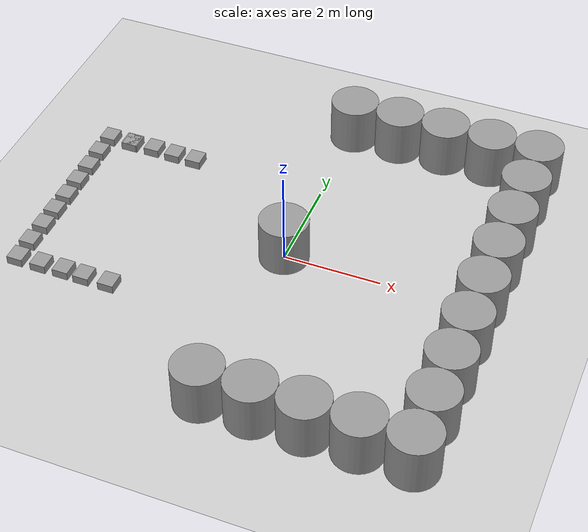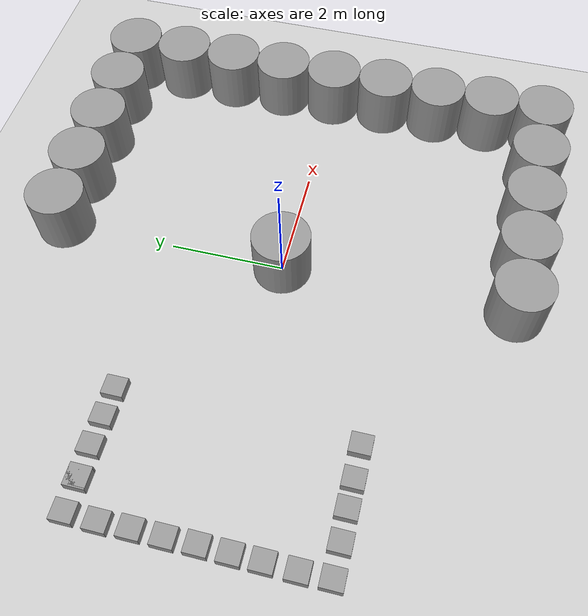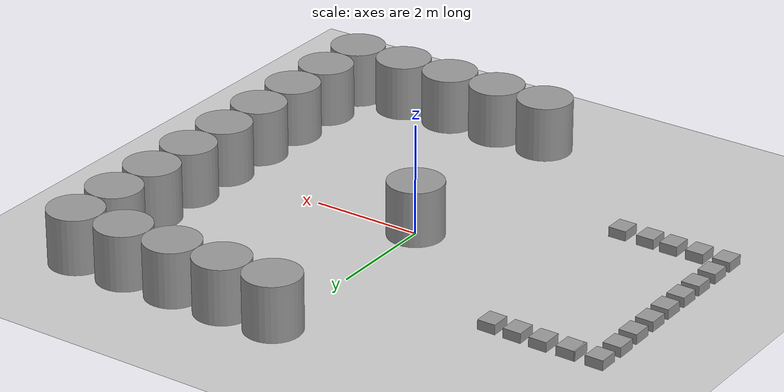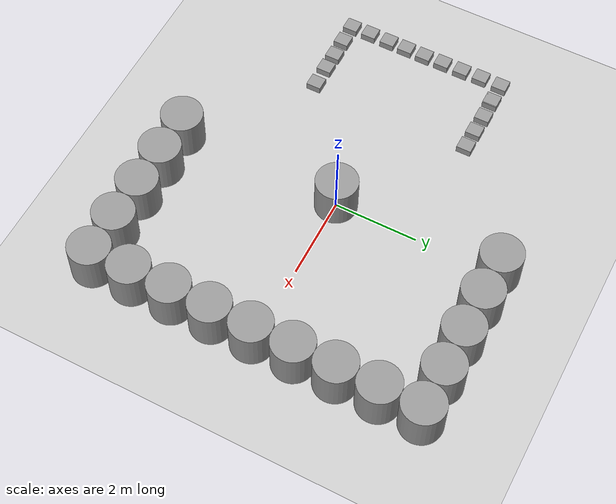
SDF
<sdf version="1.7">
 <world name="default">
  <light name="sun" type="directional">
   <pose>0 0 10 0 -0 0</pose>
   <diffuse>0.8 0.8 0.8 1</diffuse>
   <specular>0.2 0.2 0.2 1</specular>
   <attenuation>
    <range>1000</range>
    <constant>0.9</constant>
    <linear>0.01</linear>
    <quadratic>0.001</quadratic>
   </attenuation>
   <direction>-0.5 0.1 -0.9</direction>
   <spot><inner_angle>0</inner_angle><outer_angle>0</outer_angle><falloff>0</falloff></spot>
  </light>
  <model name="ground_plane">
   <static>1</static>
   <link name="link">
    <collision name="collision">
     <geometry><plane><normal>0 0 1</normal><size>100 100</size></plane></geometry>
     <surface>
      <contact><collide_bitmask>65535</collide_bitmask></contact>
      <friction><ode><mu>100</mu><mu2>50</mu2></ode></friction>
     </surface>
    </collision>
    <visual name="visual">
     <cast_shadows>0</cast_shadows>
     <geometry><plane><normal>0 0 1</normal><size>100 100</size></plane></geometry>
     <material>
      <script><uri>file://media/materials/scripts/gazebo.material</uri><name>Gazebo/Grey</name></script>
     </material>
    </visual>
   </link>
  </model>
  <gravity>0 0 -9.8</gravity>
  <magnetic_field>6e-06 2.3e-05 -4.2e-05</magnetic_field>
  <atmosphere type="adiabatic"/>
  <physics type="ode">
   <max_step_size>0.001</max_step_size>
   <real_time_factor>1</real_time_factor>
   <real_time_update_rate>1000</real_time_update_rate>
  </physics>
  <scene><ambient>0.4 0.4 0.4 1</ambient><background>0.7 0.7 0.7 1</background><shadows>1</shadows></scene>
  <spherical_coordinates>
   <surface_model>EARTH_WGS84</surface_model>
   <latitude_deg>0</latitude_deg>
   <longitude_deg>0</longitude_deg>
   <elevation>0</elevation>
   <heading_deg>0</heading_deg>
  </spherical_coordinates>
  <model name="cylinder_1m">
   <model name="cylinder_1m">
    <link name="link_0">
     <inertial>
      <mass>1</mass>
      <inertia>
       <ixx>0.166667</ixx>
       <ixy>0</ixy>
       <ixz>0</ixz>
       <iyy>0.166667</iyy>
       <iyz>0</iyz>
       <izz>0.166667</izz>
      </inertia>
     </inertial>
     <pose>0 0 -0 1.5708 -0 0</pose>
     <visual name="visual">
      <geometry>
       <mesh>
        <uri>/home/leesirius/workbench_ws/src/tb3_custom_worlds/custom_models/cylinder_1m.obj</uri>
        <scale>1 1 1</scale>
       </mesh>
      </geometry>
      <material>
       <lighting>1</lighting>
       <script><uri>file://media/materials/scripts/gazebo.material</uri><name>Gazebo/Grey</name></script>
       <shader type="pixel"/>
      </material>
     </visual>
     <collision name="collision">
      <geometry>
       <mesh>
        <uri>/home/leesirius/workbench_ws/src/tb3_custom_worlds/custom_models/cylinder_1m.obj</uri>
        <scale>1 1 1</scale>
       </mesh>
      </geometry>
      <surface>
       <friction>
        <ode><mu>1</mu><mu2>1</mu2><fdir1>0 0 0</fdir1><slip1>0</slip1><slip2>0</slip2></ode>
        <torsional>
         <coefficient>1</coefficient>
         <patch_radius>0</patch_radius>
         <surface_radius>0</surface_radius>
         <use_patch_radius>1</use_patch_radius>
         <ode><slip>0</slip></ode>
        </torsional>
       </friction>
       <bounce><restitution_coefficient>0</restitution_coefficient><threshold>1e+06</threshold></bounce>
       <contact>
        <collide_without_contact>0</collide_without_contact>
        <collide_without_contact_bitmask>1</collide_without_contact_bitmask>
        <collide_bitmask>1</collide_bitmask>
        <ode>
         <soft_cfm>0</soft_cfm>
         <soft_erp>0.2</soft_erp>
         <kp>1e+13</kp>
         <kd>1</kd>
         <max_vel>0.01</max_vel>
         <min_depth>0</min_depth>
        </ode>
        <bullet>
         <split_impulse>1</split_impulse>
         <split_impulse_penetration_threshold>-0.01</split_impulse_penetration_threshold>
         <soft_cfm>0</soft_cfm>
         <soft_erp>0.2</soft_erp>
         <kp>1e+13</kp>
         <kd>1</kd>
        </bullet>
       </contact>
      </surface>
     </collision>
    </link>
    <static>0</static>
    <pose>0 0 4e-06 0 -0 0</pose>
   </model>
   <static>1</static>
   <pose>0.000129 4.00143 0.499996 -3e-06 0 0.000269</pose>
  </model>
  <model name="cylinder_1m_clone">
   <model name="cylinder_1m">
    <link name="link_0">
     <inertial>
      <mass>1</mass>
      <inertia>
       <ixx>0.166667</ixx>
       <ixy>0</ixy>
       <ixz>0</ixz>
       <iyy>0.166667</iyy>
       <iyz>0</iyz>
       <izz>0.166667</izz>
      </inertia>
     </inertial>
     <pose>0 0 -0 1.5708 -0 0</pose>
     <visual name="visual">
      <geometry>
       <mesh>
        <uri>/home/leesirius/workbench_ws/src/tb3_custom_worlds/custom_models/cylinder_1m.obj</uri>
        <scale>1 1 1</scale>
       </mesh>
      </geometry>
      <material>
       <lighting>1</lighting>
       <script><uri>file://media/materials/scripts/gazebo.material</uri><name>Gazebo/Grey</name></script>
       <shader type="pixel"/>
      </material>
     </visual>
     <collision name="collision">
      <geometry>
       <mesh>
        <uri>/home/leesirius/workbench_ws/src/tb3_custom_worlds/custom_models/cylinder_1m.obj</uri>
        <scale>1 1 1</scale>
       </mesh>
      </geometry>
      <surface>
       <friction>
        <ode><mu>1</mu><mu2>1</mu2><fdir1>0 0 0</fdir1><slip1>0</slip1><slip2>0</slip2></ode>
        <torsional>
         <coefficient>1</coefficient>
         <patch_radius>0</patch_radius>
         <surface_radius>0</surface_radius>
         <use_patch_radius>1</use_patch_radius>
         <ode><slip>0</slip></ode>
        </torsional>
       </friction>
       <bounce><restitution_coefficient>0</restitution_coefficient><threshold>1e+06</threshold></bounce>
       <contact>
        <collide_without_contact>0</collide_without_contact>
        <collide_without_contact_bitmask>1</collide_without_contact_bitmask>
        <collide_bitmask>1</collide_bitmask>
        <ode>
         <soft_cfm>0</soft_cfm>
         <soft_erp>0.2</soft_erp>
         <kp>1e+13</kp>
         <kd>1</kd>
         <max_vel>0.01</max_vel>
         <min_depth>0</min_depth>
        </ode>
        <bullet>
         <split_impulse>1</split_impulse>
         <split_impulse_penetration_threshold>-0.01</split_impulse_penetration_threshold>
         <soft_cfm>0</soft_cfm>
         <soft_erp>0.2</soft_erp>
         <kp>1e+13</kp>
         <kd>1</kd>
        </bullet>
       </contact>
      </surface>
     </collision>
    </link>
    <static>0</static>
    <pose>0 0 4e-06 0 -0 0</pose>
   </model>
   <static>1</static>
   <pose>1.00003 3.99999 0.499993 -4e-06 -7e-06 0.000153</pose>
  </model>
  <model name="cylinder_1m_clone_0">
   <model name="cylinder_1m">
    <link name="link_0">
     <inertial>
      <mass>1</mass>
      <inertia>
       <ixx>0.166667</ixx>
       <ixy>0</ixy>
       <ixz>0</ixz>
       <iyy>0.166667</iyy>
       <iyz>0</iyz>
       <izz>0.166667</izz>
      </inertia>
     </inertial>
     <pose>0 0 -0 1.5708 -0 0</pose>
     <visual name="visual">
      <geometry>
       <mesh>
        <uri>/home/leesirius/workbench_ws/src/tb3_custom_worlds/custom_models/cylinder_1m.obj</uri>
        <scale>1 1 1</scale>
       </mesh>
      </geometry>
      <material>
       <lighting>1</lighting>
       <script><uri>file://media/materials/scripts/gazebo.material</uri><name>Gazebo/Grey</name></script>
       <shader type="pixel"/>
      </material>
     </visual>
     <collision name="collision">
      <geometry>
       <mesh>
        <uri>/home/leesirius/workbench_ws/src/tb3_custom_worlds/custom_models/cylinder_1m.obj</uri>
        <scale>1 1 1</scale>
       </mesh>
      </geometry>
      <surface>
       <friction>
        <ode><mu>1</mu><mu2>1</mu2><fdir1>0 0 0</fdir1><slip1>0</slip1><slip2>0</slip2></ode>
        <torsional>
         <coefficient>1</coefficient>
         <patch_radius>0</patch_radius>
         <surface_radius>0</surface_radius>
         <use_patch_radius>1</use_patch_radius>
         <ode><slip>0</slip></ode>
        </torsional>
       </friction>
       <bounce><restitution_coefficient>0</restitution_coefficient><threshold>1e+06</threshold></bounce>
       <contact>
        <collide_without_contact>0</collide_without_contact>
        <collide_without_contact_bitmask>1</collide_without_contact_bitmask>
        <collide_bitmask>1</collide_bitmask>
        <ode>
         <soft_cfm>0</soft_cfm>
         <soft_erp>0.2</soft_erp>
         <kp>1e+13</kp>
         <kd>1</kd>
         <max_vel>0.01</max_vel>
         <min_depth>0</min_depth>
        </ode>
        <bullet>
         <split_impulse>1</split_impulse>
         <split_impulse_penetration_threshold>-0.01</split_impulse_penetration_threshold>
         <soft_cfm>0</soft_cfm>
         <soft_erp>0.2</soft_erp>
         <kp>1e+13</kp>
         <kd>1</kd>
        </bullet>
       </contact>
      </surface>
     </collision>
    </link>
    <static>0</static>
    <pose>0 0 4e-06 0 -0 0</pose>
   </model>
   <static>1</static>
   <pose>2.00003 3.99999 0.499993 -4e-06 -7e-06 0.000153</pose>
  </model>
  <model name="cylinder_1m_clone_1">
   <model name="cylinder_1m">
    <link name="link_0">
     <inertial>
      <mass>1</mass>
      <inertia>
       <ixx>0.166667</ixx>
       <ixy>0</ixy>
       <ixz>0</ixz>
       <iyy>0.166667</iyy>
       <iyz>0</iyz>
       <izz>0.166667</izz>
      </inertia>
     </inertial>
     <pose>0 0 -0 1.5708 -0 0</pose>
     <visual name="visual">
      <geometry>
       <mesh>
        <uri>/home/leesirius/workbench_ws/src/tb3_custom_worlds/custom_models/cylinder_1m.obj</uri>
        <scale>1 1 1</scale>
       </mesh>
      </geometry>
      <material>
       <lighting>1</lighting>
       <script><uri>file://media/materials/scripts/gazebo.material</uri><name>Gazebo/Grey</name></script>
       <shader type="pixel"/>
      </material>
     </visual>
     <collision name="collision">
      <geometry>
       <mesh>
        <uri>/home/leesirius/workbench_ws/src/tb3_custom_worlds/custom_models/cylinder_1m.obj</uri>
        <scale>1 1 1</scale>
       </mesh>
      </geometry>
      <surface>
       <friction>
        <ode><mu>1</mu><mu2>1</mu2><fdir1>0 0 0</fdir1><slip1>0</slip1><slip2>0</slip2></ode>
        <torsional>
         <coefficient>1</coefficient>
         <patch_radius>0</patch_radius>
         <surface_radius>0</surface_radius>
         <use_patch_radius>1</use_patch_radius>
         <ode><slip>0</slip></ode>
        </torsional>
       </friction>
       <bounce><restitution_coefficient>0</restitution_coefficient><threshold>1e+06</threshold></bounce>
       <contact>
        <collide_without_contact>0</collide_without_contact>
        <collide_without_contact_bitmask>1</collide_without_contact_bitmask>
        <collide_bitmask>1</collide_bitmask>
        <ode>
         <soft_cfm>0</soft_cfm>
         <soft_erp>0.2</soft_erp>
         <kp>1e+13</kp>
         <kd>1</kd>
         <max_vel>0.01</max_vel>
         <min_depth>0</min_depth>
        </ode>
        <bullet>
         <split_impulse>1</split_impulse>
         <split_impulse_penetration_threshold>-0.01</split_impulse_penetration_threshold>
         <soft_cfm>0</soft_cfm>
         <soft_erp>0.2</soft_erp>
         <kp>1e+13</kp>
         <kd>1</kd>
        </bullet>
       </contact>
      </surface>
     </collision>
    </link>
    <static>0</static>
    <pose>0 0 4e-06 0 -0 0</pose>
   </model>
   <static>1</static>
   <pose>3.00003 3.99999 0.499993 -4e-06 -7e-06 0.000153</pose>
  </model>
  <model name="cylinder_1m_clone_2">
   <model name="cylinder_1m">
    <link name="link_0">
     <inertial>
      <mass>1</mass>
      <inertia>
       <ixx>0.166667</ixx>
       <ixy>0</ixy>
       <ixz>0</ixz>
       <iyy>0.166667</iyy>
       <iyz>0</iyz>
       <izz>0.166667</izz>
      </inertia>
     </inertial>
     <pose>0 0 -0 1.5708 -0 0</pose>
     <visual name="visual">
      <geometry>
       <mesh>
        <uri>/home/leesirius/workbench_ws/src/tb3_custom_worlds/custom_models/cylinder_1m.obj</uri>
        <scale>1 1 1</scale>
       </mesh>
      </geometry>
      <material>
       <lighting>1</lighting>
       <script><uri>file://media/materials/scripts/gazebo.material</uri><name>Gazebo/Grey</name></script>
       <shader type="pixel"/>
      </material>
     </visual>
     <collision name="collision">
      <geometry>
       <mesh>
        <uri>/home/leesirius/workbench_ws/src/tb3_custom_worlds/custom_models/cylinder_1m.obj</uri>
        <scale>1 1 1</scale>
       </mesh>
      </geometry>
      <surface>
       <friction>
        <ode><mu>1</mu><mu2>1</mu2><fdir1>0 0 0</fdir1><slip1>0</slip1><slip2>0</slip2></ode>
        <torsional>
         <coefficient>1</coefficient>
         <patch_radius>0</patch_radius>
         <surface_radius>0</surface_radius>
         <use_patch_radius>1</use_patch_radius>
         <ode><slip>0</slip></ode>
        </torsional>
       </friction>
       <bounce><restitution_coefficient>0</restitution_coefficient><threshold>1e+06</threshold></bounce>
       <contact>
        <collide_without_contact>0</collide_without_contact>
        <collide_without_contact_bitmask>1</collide_without_contact_bitmask>
        <collide_bitmask>1</collide_bitmask>
        <ode>
         <soft_cfm>0</soft_cfm>
         <soft_erp>0.2</soft_erp>
         <kp>1e+13</kp>
         <kd>1</kd>
         <max_vel>0.01</max_vel>
         <min_depth>0</min_depth>
        </ode>
        <bullet>
         <split_impulse>1</split_impulse>
         <split_impulse_penetration_threshold>-0.01</split_impulse_penetration_threshold>
         <soft_cfm>0</soft_cfm>
         <soft_erp>0.2</soft_erp>
         <kp>1e+13</kp>
         <kd>1</kd>
        </bullet>
       </contact>
      </surface>
     </collision>
    </link>
    <static>0</static>
    <pose>0 0 4e-06 0 -0 0</pose>
   </model>
   <static>1</static>
   <pose>4.00003 3.99999 0.499993 -4e-06 -7e-06 0.000153</pose>
  </model>
  <model name="cylinder_1m_clone_4">
   <model name="cylinder_1m">
    <link name="link_0">
     <inertial>
      <mass>1</mass>
      <inertia>
       <ixx>0.166667</ixx>
       <ixy>0</ixy>
       <ixz>0</ixz>
       <iyy>0.166667</iyy>
       <iyz>0</iyz>
       <izz>0.166667</izz>
      </inertia>
     </inertial>
     <pose>0 0 -0 1.5708 -0 0</pose>
     <visual name="visual">
      <geometry>
       <mesh>
        <uri>/home/leesirius/workbench_ws/src/tb3_custom_worlds/custom_models/cylinder_1m.obj</uri>
        <scale>1 1 1</scale>
       </mesh>
      </geometry>
      <material>
       <lighting>1</lighting>
       <script><uri>file://media/materials/scripts/gazebo.material</uri><name>Gazebo/Grey</name></script>
       <shader type="pixel"/>
      </material>
     </visual>
     <collision name="collision">
      <geometry>
       <mesh>
        <uri>/home/leesirius/workbench_ws/src/tb3_custom_worlds/custom_models/cylinder_1m.obj</uri>
        <scale>1 1 1</scale>
       </mesh>
      </geometry>
      <surface>
       <friction>
        <ode><mu>1</mu><mu2>1</mu2><fdir1>0 0 0</fdir1><slip1>0</slip1><slip2>0</slip2></ode>
        <torsional>
         <coefficient>1</coefficient>
         <patch_radius>0</patch_radius>
         <surface_radius>0</surface_radius>
         <use_patch_radius>1</use_patch_radius>
         <ode><slip>0</slip></ode>
        </torsional>
       </friction>
       <bounce><restitution_coefficient>0</restitution_coefficient><threshold>1e+06</threshold></bounce>
       <contact>
        <collide_without_contact>0</collide_without_contact>
        <collide_without_contact_bitmask>1</collide_without_contact_bitmask>
        <collide_bitmask>1</collide_bitmask>
        <ode>
         <soft_cfm>0</soft_cfm>
         <soft_erp>0.2</soft_erp>
         <kp>1e+13</kp>
         <kd>1</kd>
         <max_vel>0.01</max_vel>
         <min_depth>0</min_depth>
        </ode>
        <bullet>
         <split_impulse>1</split_impulse>
         <split_impulse_penetration_threshold>-0.01</split_impulse_penetration_threshold>
         <soft_cfm>0</soft_cfm>
         <soft_erp>0.2</soft_erp>
         <kp>1e+13</kp>
         <kd>1</kd>
        </bullet>
       </contact>
      </surface>
     </collision>
    </link>
    <static>0</static>
    <pose>0 0 4e-06 0 -0 0</pose>
   </model>
   <static>1</static>
   <pose>4.00003 2.99999 0.499993 -4e-06 -7e-06 0.000153</pose>
  </model>
  <model name="cylinder_1m_clone_5">
   <model name="cylinder_1m">
    <link name="link_0">
     <inertial>
      <mass>1</mass>
      <inertia>
       <ixx>0.166667</ixx>
       <ixy>0</ixy>
       <ixz>0</ixz>
       <iyy>0.166667</iyy>
       <iyz>0</iyz>
       <izz>0.166667</izz>
      </inertia>
     </inertial>
     <pose>0 0 -0 1.5708 -0 0</pose>
     <visual name="visual">
      <geometry>
       <mesh>
        <uri>/home/leesirius/workbench_ws/src/tb3_custom_worlds/custom_models/cylinder_1m.obj</uri>
        <scale>1 1 1</scale>
       </mesh>
      </geometry>
      <material>
       <lighting>1</lighting>
       <script><uri>file://media/materials/scripts/gazebo.material</uri><name>Gazebo/Grey</name></script>
       <shader type="pixel"/>
      </material>
     </visual>
     <collision name="collision">
      <geometry>
       <mesh>
        <uri>/home/leesirius/workbench_ws/src/tb3_custom_worlds/custom_models/cylinder_1m.obj</uri>
        <scale>1 1 1</scale>
       </mesh>
      </geometry>
      <surface>
       <friction>
        <ode><mu>1</mu><mu2>1</mu2><fdir1>0 0 0</fdir1><slip1>0</slip1><slip2>0</slip2></ode>
        <torsional>
         <coefficient>1</coefficient>
         <patch_radius>0</patch_radius>
         <surface_radius>0</surface_radius>
         <use_patch_radius>1</use_patch_radius>
         <ode><slip>0</slip></ode>
        </torsional>
       </friction>
       <bounce><restitution_coefficient>0</restitution_coefficient><threshold>1e+06</threshold></bounce>
       <contact>
        <collide_without_contact>0</collide_without_contact>
        <collide_without_contact_bitmask>1</collide_without_contact_bitmask>
        <collide_bitmask>1</collide_bitmask>
        <ode>
         <soft_cfm>0</soft_cfm>
         <soft_erp>0.2</soft_erp>
         <kp>1e+13</kp>
         <kd>1</kd>
         <max_vel>0.01</max_vel>
         <min_depth>0</min_depth>
        </ode>
        <bullet>
         <split_impulse>1</split_impulse>
         <split_impulse_penetration_threshold>-0.01</split_impulse_penetration_threshold>
         <soft_cfm>0</soft_cfm>
         <soft_erp>0.2</soft_erp>
         <kp>1e+13</kp>
         <kd>1</kd>
        </bullet>
       </contact>
      </surface>
     </collision>
    </link>
    <static>0</static>
    <pose>0 0 4e-06 0 -0 0</pose>
   </model>
   <static>1</static>
   <pose>4.00003 1.99999 0.499993 -4e-06 -7e-06 0.000153</pose>
  </model>
  <model name="cylinder_1m_clone_6">
   <model name="cylinder_1m">
    <link name="link_0">
     <inertial>
      <mass>1</mass>
      <inertia>
       <ixx>0.166667</ixx>
       <ixy>0</ixy>
       <ixz>0</ixz>
       <iyy>0.166667</iyy>
       <iyz>0</iyz>
       <izz>0.166667</izz>
      </inertia>
     </inertial>
     <pose>0 0 -0 1.5708 -0 0</pose>
     <visual name="visual">
      <geometry>
       <mesh>
        <uri>/home/leesirius/workbench_ws/src/tb3_custom_worlds/custom_models/cylinder_1m.obj</uri>
        <scale>1 1 1</scale>
       </mesh>
      </geometry>
      <material>
       <lighting>1</lighting>
       <script><uri>file://media/materials/scripts/gazebo.material</uri><name>Gazebo/Grey</name></script>
       <shader type="pixel"/>
      </material>
     </visual>
     <collision name="collision">
      <geometry>
       <mesh>
        <uri>/home/leesirius/workbench_ws/src/tb3_custom_worlds/custom_models/cylinder_1m.obj</uri>
        <scale>1 1 1</scale>
       </mesh>
      </geometry>
      <surface>
       <friction>
        <ode><mu>1</mu><mu2>1</mu2><fdir1>0 0 0</fdir1><slip1>0</slip1><slip2>0</slip2></ode>
        <torsional>
         <coefficient>1</coefficient>
         <patch_radius>0</patch_radius>
         <surface_radius>0</surface_radius>
         <use_patch_radius>1</use_patch_radius>
         <ode><slip>0</slip></ode>
        </torsional>
       </friction>
       <bounce><restitution_coefficient>0</restitution_coefficient><threshold>1e+06</threshold></bounce>
       <contact>
        <collide_without_contact>0</collide_without_contact>
        <collide_without_contact_bitmask>1</collide_without_contact_bitmask>
        <collide_bitmask>1</collide_bitmask>
        <ode>
         <soft_cfm>0</soft_cfm>
         <soft_erp>0.2</soft_erp>
         <kp>1e+13</kp>
         <kd>1</kd>
         <max_vel>0.01</max_vel>
         <min_depth>0</min_depth>
        </ode>
        <bullet>
         <split_impulse>1</split_impulse>
         <split_impulse_penetration_threshold>-0.01</split_impulse_penetration_threshold>
         <soft_cfm>0</soft_cfm>
         <soft_erp>0.2</soft_erp>
         <kp>1e+13</kp>
         <kd>1</kd>
        </bullet>
       </contact>
      </surface>
     </collision>
    </link>
    <static>0</static>
    <pose>0 0 4e-06 0 -0 0</pose>
   </model>
   <static>1</static>
   <pose>4.00003 0.999985 0.499993 -4e-06 -7e-06 0.000153</pose>
  </model>
  <model name="cylinder_1m_clone_7">
   <model name="cylinder_1m">
    <link name="link_0">
     <inertial>
      <mass>1</mass>
      <inertia>
       <ixx>0.166667</ixx>
       <ixy>0</ixy>
       <ixz>0</ixz>
       <iyy>0.166667</iyy>
       <iyz>0</iyz>
       <izz>0.166667</izz>
      </inertia>
     </inertial>
     <pose>0 0 -0 1.5708 -0 0</pose>
     <visual name="visual">
      <geometry>
       <mesh>
        <uri>/home/leesirius/workbench_ws/src/tb3_custom_worlds/custom_models/cylinder_1m.obj</uri>
        <scale>1 1 1</scale>
       </mesh>
      </geometry>
      <material>
       <lighting>1</lighting>
       <script><uri>file://media/materials/scripts/gazebo.material</uri><name>Gazebo/Grey</name></script>
       <shader type="pixel"/>
      </material>
     </visual>
     <collision name="collision">
      <geometry>
       <mesh>
        <uri>/home/leesirius/workbench_ws/src/tb3_custom_worlds/custom_models/cylinder_1m.obj</uri>
        <scale>1 1 1</scale>
       </mesh>
      </geometry>
      <surface>
       <friction>
        <ode><mu>1</mu><mu2>1</mu2><fdir1>0 0 0</fdir1><slip1>0</slip1><slip2>0</slip2></ode>
        <torsional>
         <coefficient>1</coefficient>
         <patch_radius>0</patch_radius>
         <surface_radius>0</surface_radius>
         <use_patch_radius>1</use_patch_radius>
         <ode><slip>0</slip></ode>
        </torsional>
       </friction>
       <bounce><restitution_coefficient>0</restitution_coefficient><threshold>1e+06</threshold></bounce>
       <contact>
        <collide_without_contact>0</collide_without_contact>
        <collide_without_contact_bitmask>1</collide_without_contact_bitmask>
        <collide_bitmask>1</collide_bitmask>
        <ode>
         <soft_cfm>0</soft_cfm>
         <soft_erp>0.2</soft_erp>
         <kp>1e+13</kp>
         <kd>1</kd>
         <max_vel>0.01</max_vel>
         <min_depth>0</min_depth>
        </ode>
        <bullet>
         <split_impulse>1</split_impulse>
         <split_impulse_penetration_threshold>-0.01</split_impulse_penetration_threshold>
         <soft_cfm>0</soft_cfm>
         <soft_erp>0.2</soft_erp>
         <kp>1e+13</kp>
         <kd>1</kd>
        </bullet>
       </contact>
      </surface>
     </collision>
    </link>
    <static>0</static>
    <pose>0 0 4e-06 0 -0 0</pose>
   </model>
   <static>1</static>
   <pose>4.00003 -1.5e-05 0.499993 -4e-06 -7e-06 0.000153</pose>
  </model>
  <model name="cylinder_1m_clone_8">
   <model name="cylinder_1m">
    <link name="link_0">
     <inertial>
      <mass>1</mass>
      <inertia>
       <ixx>0.166667</ixx>
       <ixy>0</ixy>
       <ixz>0</ixz>
       <iyy>0.166667</iyy>
       <iyz>0</iyz>
       <izz>0.166667</izz>
      </inertia>
     </inertial>
     <pose>0 0 -0 1.5708 -0 0</pose>
     <visual name="visual">
      <geometry>
       <mesh>
        <uri>/home/leesirius/workbench_ws/src/tb3_custom_worlds/custom_models/cylinder_1m.obj</uri>
        <scale>1 1 1</scale>
       </mesh>
      </geometry>
      <material>
       <lighting>1</lighting>
       <script><uri>file://media/materials/scripts/gazebo.material</uri><name>Gazebo/Grey</name></script>
       <shader type="pixel"/>
      </material>
     </visual>
     <collision name="collision">
      <geometry>
       <mesh>
        <uri>/home/leesirius/workbench_ws/src/tb3_custom_worlds/custom_models/cylinder_1m.obj</uri>
        <scale>1 1 1</scale>
       </mesh>
      </geometry>
      <surface>
       <friction>
        <ode><mu>1</mu><mu2>1</mu2><fdir1>0 0 0</fdir1><slip1>0</slip1><slip2>0</slip2></ode>
        <torsional>
         <coefficient>1</coefficient>
         <patch_radius>0</patch_radius>
         <surface_radius>0</surface_radius>
         <use_patch_radius>1</use_patch_radius>
         <ode><slip>0</slip></ode>
        </torsional>
       </friction>
       <bounce><restitution_coefficient>0</restitution_coefficient><threshold>1e+06</threshold></bounce>
       <contact>
        <collide_without_contact>0</collide_without_contact>
        <collide_without_contact_bitmask>1</collide_without_contact_bitmask>
        <collide_bitmask>1</collide_bitmask>
        <ode>
         <soft_cfm>0</soft_cfm>
         <soft_erp>0.2</soft_erp>
         <kp>1e+13</kp>
         <kd>1</kd>
         <max_vel>0.01</max_vel>
         <min_depth>0</min_depth>
        </ode>
        <bullet>
         <split_impulse>1</split_impulse>
         <split_impulse_penetration_threshold>-0.01</split_impulse_penetration_threshold>
         <soft_cfm>0</soft_cfm>
         <soft_erp>0.2</soft_erp>
         <kp>1e+13</kp>
         <kd>1</kd>
        </bullet>
       </contact>
      </surface>
     </collision>
    </link>
    <static>0</static>
    <pose>0 0 4e-06 0 -0 0</pose>
   </model>
   <static>1</static>
   <pose>4.00003 -1.00001 0.499993 -4e-06 -7e-06 0.000153</pose>
  </model>
  <model name="cylinder_1m_clone_9">
   <model name="cylinder_1m">
    <link name="link_0">
     <inertial>
      <mass>1</mass>
      <inertia>
       <ixx>0.166667</ixx>
       <ixy>0</ixy>
       <ixz>0</ixz>
       <iyy>0.166667</iyy>
       <iyz>0</iyz>
       <izz>0.166667</izz>
      </inertia>
     </inertial>
     <pose>0 0 -0 1.5708 -0 0</pose>
     <visual name="visual">
      <geometry>
       <mesh>
        <uri>/home/leesirius/workbench_ws/src/tb3_custom_worlds/custom_models/cylinder_1m.obj</uri>
        <scale>1 1 1</scale>
       </mesh>
      </geometry>
      <material>
       <lighting>1</lighting>
       <script><uri>file://media/materials/scripts/gazebo.material</uri><name>Gazebo/Grey</name></script>
       <shader type="pixel"/>
      </material>
     </visual>
     <collision name="collision">
      <geometry>
       <mesh>
        <uri>/home/leesirius/workbench_ws/src/tb3_custom_worlds/custom_models/cylinder_1m.obj</uri>
        <scale>1 1 1</scale>
       </mesh>
      </geometry>
      <surface>
       <friction>
        <ode><mu>1</mu><mu2>1</mu2><fdir1>0 0 0</fdir1><slip1>0</slip1><slip2>0</slip2></ode>
        <torsional>
         <coefficient>1</coefficient>
         <patch_radius>0</patch_radius>
         <surface_radius>0</surface_radius>
         <use_patch_radius>1</use_patch_radius>
         <ode><slip>0</slip></ode>
        </torsional>
       </friction>
       <bounce><restitution_coefficient>0</restitution_coefficient><threshold>1e+06</threshold></bounce>
       <contact>
        <collide_without_contact>0</collide_without_contact>
        <collide_without_contact_bitmask>1</collide_without_contact_bitmask>
        <collide_bitmask>1</collide_bitmask>
        <ode>
         <soft_cfm>0</soft_cfm>
         <soft_erp>0.2</soft_erp>
         <kp>1e+13</kp>
         <kd>1</kd>
         <max_vel>0.01</max_vel>
         <min_depth>0</min_depth>
        </ode>
        <bullet>
         <split_impulse>1</split_impulse>
         <split_impulse_penetration_threshold>-0.01</split_impulse_penetration_threshold>
         <soft_cfm>0</soft_cfm>
         <soft_erp>0.2</soft_erp>
         <kp>1e+13</kp>
         <kd>1</kd>
        </bullet>
       </contact>
      </surface>
     </collision>
    </link>
    <static>0</static>
    <pose>0 0 4e-06 0 -0 0</pose>
   </model>
   <static>1</static>
   <pose>4.00003 -2.00001 0.499993 -4e-06 -7e-06 0.000153</pose>
  </model>
  <model name="cylinder_1m_clone_10">
   <model name="cylinder_1m">
    <link name="link_0">
     <inertial>
      <mass>1</mass>
      <inertia>
       <ixx>0.166667</ixx>
       <ixy>0</ixy>
       <ixz>0</ixz>
       <iyy>0.166667</iyy>
       <iyz>0</iyz>
       <izz>0.166667</izz>
      </inertia>
     </inertial>
     <pose>0 0 -0 1.5708 -0 0</pose>
     <visual name="visual">
      <geometry>
       <mesh>
        <uri>/home/leesirius/workbench_ws/src/tb3_custom_worlds/custom_models/cylinder_1m.obj</uri>
        <scale>1 1 1</scale>
       </mesh>
      </geometry>
      <material>
       <lighting>1</lighting>
       <script><uri>file://media/materials/scripts/gazebo.material</uri><name>Gazebo/Grey</name></script>
       <shader type="pixel"/>
      </material>
     </visual>
     <collision name="collision">
      <geometry>
       <mesh>
        <uri>/home/leesirius/workbench_ws/src/tb3_custom_worlds/custom_models/cylinder_1m.obj</uri>
        <scale>1 1 1</scale>
       </mesh>
      </geometry>
      <surface>
       <friction>
        <ode><mu>1</mu><mu2>1</mu2><fdir1>0 0 0</fdir1><slip1>0</slip1><slip2>0</slip2></ode>
        <torsional>
         <coefficient>1</coefficient>
         <patch_radius>0</patch_radius>
         <surface_radius>0</surface_radius>
         <use_patch_radius>1</use_patch_radius>
         <ode><slip>0</slip></ode>
        </torsional>
       </friction>
       <bounce><restitution_coefficient>0</restitution_coefficient><threshold>1e+06</threshold></bounce>
       <contact>
        <collide_without_contact>0</collide_without_contact>
        <collide_without_contact_bitmask>1</collide_without_contact_bitmask>
        <collide_bitmask>1</collide_bitmask>
        <ode>
         <soft_cfm>0</soft_cfm>
         <soft_erp>0.2</soft_erp>
         <kp>1e+13</kp>
         <kd>1</kd>
         <max_vel>0.01</max_vel>
         <min_depth>0</min_depth>
        </ode>
        <bullet>
         <split_impulse>1</split_impulse>
         <split_impulse_penetration_threshold>-0.01</split_impulse_penetration_threshold>
         <soft_cfm>0</soft_cfm>
         <soft_erp>0.2</soft_erp>
         <kp>1e+13</kp>
         <kd>1</kd>
        </bullet>
       </contact>
      </surface>
     </collision>
    </link>
    <static>0</static>
    <pose>0 0 4e-06 0 -0 0</pose>
   </model>
   <static>1</static>
   <pose>4.00003 -3.00001 0.499993 -4e-06 -7e-06 0.000153</pose>
  </model>
  <model name="cylinder_1m_clone_11">
   <model name="cylinder_1m">
    <link name="link_0">
     <inertial>
      <mass>1</mass>
      <inertia>
       <ixx>0.166667</ixx>
       <ixy>0</ixy>
       <ixz>0</ixz>
       <iyy>0.166667</iyy>
       <iyz>0</iyz>
       <izz>0.166667</izz>
      </inertia>
     </inertial>
     <pose>0 0 -0 1.5708 -0 0</pose>
     <visual name="visual">
      <geometry>
       <mesh>
        <uri>/home/leesirius/workbench_ws/src/tb3_custom_worlds/custom_models/cylinder_1m.obj</uri>
        <scale>1 1 1</scale>
       </mesh>
      </geometry>
      <material>
       <lighting>1</lighting>
       <script><uri>file://media/materials/scripts/gazebo.material</uri><name>Gazebo/Grey</name></script>
       <shader type="pixel"/>
      </material>
     </visual>
     <collision name="collision">
      <geometry>
       <mesh>
        <uri>/home/leesirius/workbench_ws/src/tb3_custom_worlds/custom_models/cylinder_1m.obj</uri>
        <scale>1 1 1</scale>
       </mesh>
      </geometry>
      <surface>
       <friction>
        <ode><mu>1</mu><mu2>1</mu2><fdir1>0 0 0</fdir1><slip1>0</slip1><slip2>0</slip2></ode>
        <torsional>
         <coefficient>1</coefficient>
         <patch_radius>0</patch_radius>
         <surface_radius>0</surface_radius>
         <use_patch_radius>1</use_patch_radius>
         <ode><slip>0</slip></ode>
        </torsional>
       </friction>
       <bounce><restitution_coefficient>0</restitution_coefficient><threshold>1e+06</threshold></bounce>
       <contact>
        <collide_without_contact>0</collide_without_contact>
        <collide_without_contact_bitmask>1</collide_without_contact_bitmask>
        <collide_bitmask>1</collide_bitmask>
        <ode>
         <soft_cfm>0</soft_cfm>
         <soft_erp>0.2</soft_erp>
         <kp>1e+13</kp>
         <kd>1</kd>
         <max_vel>0.01</max_vel>
         <min_depth>0</min_depth>
        </ode>
        <bullet>
         <split_impulse>1</split_impulse>
         <split_impulse_penetration_threshold>-0.01</split_impulse_penetration_threshold>
         <soft_cfm>0</soft_cfm>
         <soft_erp>0.2</soft_erp>
         <kp>1e+13</kp>
         <kd>1</kd>
        </bullet>
       </contact>
      </surface>
     </collision>
    </link>
    <static>0</static>
    <pose>0 0 4e-06 0 -0 0</pose>
   </model>
   <static>1</static>
   <pose>4.00003 -4.00001 0.499993 -4e-06 -7e-06 0.000153</pose>
  </model>
  <model name="cylinder_1m_clone_12">
   <model name="cylinder_1m">
    <link name="link_0">
     <inertial>
      <mass>1</mass>
      <inertia>
       <ixx>0.166667</ixx>
       <ixy>0</ixy>
       <ixz>0</ixz>
       <iyy>0.166667</iyy>
       <iyz>0</iyz>
       <izz>0.166667</izz>
      </inertia>
     </inertial>
     <pose>0 0 -0 1.5708 -0 0</pose>
     <visual name="visual">
      <geometry>
       <mesh>
        <uri>/home/leesirius/workbench_ws/src/tb3_custom_worlds/custom_models/cylinder_1m.obj</uri>
        <scale>1 1 1</scale>
       </mesh>
      </geometry>
      <material>
       <lighting>1</lighting>
       <script><uri>file://media/materials/scripts/gazebo.material</uri><name>Gazebo/Grey</name></script>
       <shader type="pixel"/>
      </material>
     </visual>
     <collision name="collision">
      <geometry>
       <mesh>
        <uri>/home/leesirius/workbench_ws/src/tb3_custom_worlds/custom_models/cylinder_1m.obj</uri>
        <scale>1 1 1</scale>
       </mesh>
      </geometry>
      <surface>
       <friction>
        <ode><mu>1</mu><mu2>1</mu2><fdir1>0 0 0</fdir1><slip1>0</slip1><slip2>0</slip2></ode>
        <torsional>
         <coefficient>1</coefficient>
         <patch_radius>0</patch_radius>
         <surface_radius>0</surface_radius>
         <use_patch_radius>1</use_patch_radius>
         <ode><slip>0</slip></ode>
        </torsional>
       </friction>
       <bounce><restitution_coefficient>0</restitution_coefficient><threshold>1e+06</threshold></bounce>
       <contact>
        <collide_without_contact>0</collide_without_contact>
        <collide_without_contact_bitmask>1</collide_without_contact_bitmask>
        <collide_bitmask>1</collide_bitmask>
        <ode>
         <soft_cfm>0</soft_cfm>
         <soft_erp>0.2</soft_erp>
         <kp>1e+13</kp>
         <kd>1</kd>
         <max_vel>0.01</max_vel>
         <min_depth>0</min_depth>
        </ode>
        <bullet>
         <split_impulse>1</split_impulse>
         <split_impulse_penetration_threshold>-0.01</split_impulse_penetration_threshold>
         <soft_cfm>0</soft_cfm>
         <soft_erp>0.2</soft_erp>
         <kp>1e+13</kp>
         <kd>1</kd>
        </bullet>
       </contact>
      </surface>
     </collision>
    </link>
    <static>0</static>
    <pose>0 0 4e-06 0 -0 0</pose>
   </model>
   <static>1</static>
   <pose>3.00003 -4.00001 0.499993 -4e-06 -7e-06 0.000153</pose>
  </model>
  <model name="cylinder_1m_clone_13">
   <model name="cylinder_1m">
    <link name="link_0">
     <inertial>
      <mass>1</mass>
      <inertia>
       <ixx>0.166667</ixx>
       <ixy>0</ixy>
       <ixz>0</ixz>
       <iyy>0.166667</iyy>
       <iyz>0</iyz>
       <izz>0.166667</izz>
      </inertia>
     </inertial>
     <pose>0 0 -0 1.5708 -0 0</pose>
     <visual name="visual">
      <geometry>
       <mesh>
        <uri>/home/leesirius/workbench_ws/src/tb3_custom_worlds/custom_models/cylinder_1m.obj</uri>
        <scale>1 1 1</scale>
       </mesh>
      </geometry>
      <material>
       <lighting>1</lighting>
       <script><uri>file://media/materials/scripts/gazebo.material</uri><name>Gazebo/Grey</name></script>
       <shader type="pixel"/>
      </material>
     </visual>
     <collision name="collision">
      <geometry>
       <mesh>
        <uri>/home/leesirius/workbench_ws/src/tb3_custom_worlds/custom_models/cylinder_1m.obj</uri>
        <scale>1 1 1</scale>
       </mesh>
      </geometry>
      <surface>
       <friction>
        <ode><mu>1</mu><mu2>1</mu2><fdir1>0 0 0</fdir1><slip1>0</slip1><slip2>0</slip2></ode>
        <torsional>
         <coefficient>1</coefficient>
         <patch_radius>0</patch_radius>
         <surface_radius>0</surface_radius>
         <use_patch_radius>1</use_patch_radius>
         <ode><slip>0</slip></ode>
        </torsional>
       </friction>
       <bounce><restitution_coefficient>0</restitution_coefficient><threshold>1e+06</threshold></bounce>
       <contact>
        <collide_without_contact>0</collide_without_contact>
        <collide_without_contact_bitmask>1</collide_without_contact_bitmask>
        <collide_bitmask>1</collide_bitmask>
        <ode>
         <soft_cfm>0</soft_cfm>
         <soft_erp>0.2</soft_erp>
         <kp>1e+13</kp>
         <kd>1</kd>
         <max_vel>0.01</max_vel>
         <min_depth>0</min_depth>
        </ode>
        <bullet>
         <split_impulse>1</split_impulse>
         <split_impulse_penetration_threshold>-0.01</split_impulse_penetration_threshold>
         <soft_cfm>0</soft_cfm>
         <soft_erp>0.2</soft_erp>
         <kp>1e+13</kp>
         <kd>1</kd>
        </bullet>
       </contact>
      </surface>
     </collision>
    </link>
    <static>0</static>
    <pose>0 0 4e-06 0 -0 0</pose>
   </model>
   <static>1</static>
   <pose>2.00003 -4.00001 0.499993 -4e-06 -7e-06 0.000153</pose>
  </model>
  <model name="cylinder_1m_clone_14">
   <model name="cylinder_1m">
    <link name="link_0">
     <inertial>
      <mass>1</mass>
      <inertia>
       <ixx>0.166667</ixx>
       <ixy>0</ixy>
       <ixz>0</ixz>
       <iyy>0.166667</iyy>
       <iyz>0</iyz>
       <izz>0.166667</izz>
      </inertia>
     </inertial>
     <pose>0 0 -0 1.5708 -0 0</pose>
     <visual name="visual">
      <geometry>
       <mesh>
        <uri>/home/leesirius/workbench_ws/src/tb3_custom_worlds/custom_models/cylinder_1m.obj</uri>
        <scale>1 1 1</scale>
       </mesh>
      </geometry>
      <material>
       <lighting>1</lighting>
       <script><uri>file://media/materials/scripts/gazebo.material</uri><name>Gazebo/Grey</name></script>
       <shader type="pixel"/>
      </material>
     </visual>
     <collision name="collision">
      <geometry>
       <mesh>
        <uri>/home/leesirius/workbench_ws/src/tb3_custom_worlds/custom_models/cylinder_1m.obj</uri>
        <scale>1 1 1</scale>
       </mesh>
      </geometry>
      <surface>
       <friction>
        <ode><mu>1</mu><mu2>1</mu2><fdir1>0 0 0</fdir1><slip1>0</slip1><slip2>0</slip2></ode>
        <torsional>
         <coefficient>1</coefficient>
         <patch_radius>0</patch_radius>
         <surface_radius>0</surface_radius>
         <use_patch_radius>1</use_patch_radius>
         <ode><slip>0</slip></ode>
        </torsional>
       </friction>
       <bounce><restitution_coefficient>0</restitution_coefficient><threshold>1e+06</threshold></bounce>
       <contact>
        <collide_without_contact>0</collide_without_contact>
        <collide_without_contact_bitmask>1</collide_without_contact_bitmask>
        <collide_bitmask>1</collide_bitmask>
        <ode>
         <soft_cfm>0</soft_cfm>
         <soft_erp>0.2</soft_erp>
         <kp>1e+13</kp>
         <kd>1</kd>
         <max_vel>0.01</max_vel>
         <min_depth>0</min_depth>
        </ode>
        <bullet>
         <split_impulse>1</split_impulse>
         <split_impulse_penetration_threshold>-0.01</split_impulse_penetration_threshold>
         <soft_cfm>0</soft_cfm>
         <soft_erp>0.2</soft_erp>
         <kp>1e+13</kp>
         <kd>1</kd>
        </bullet>
       </contact>
      </surface>
     </collision>
    </link>
    <static>0</static>
    <pose>0 0 4e-06 0 -0 0</pose>
   </model>
   <static>1</static>
   <pose>1.00003 -4.00001 0.499993 -4e-06 -7e-06 0.000153</pose>
  </model>
  <model name="cylinder_1m_clone_15">
   <model name="cylinder_1m">
    <link name="link_0">
     <inertial>
      <mass>1</mass>
      <inertia>
       <ixx>0.166667</ixx>
       <ixy>0</ixy>
       <ixz>0</ixz>
       <iyy>0.166667</iyy>
       <iyz>0</iyz>
       <izz>0.166667</izz>
      </inertia>
     </inertial>
     <pose>0 0 -0 1.5708 -0 0</pose>
     <visual name="visual">
      <geometry>
       <mesh>
        <uri>/home/leesirius/workbench_ws/src/tb3_custom_worlds/custom_models/cylinder_1m.obj</uri>
        <scale>1 1 1</scale>
       </mesh>
      </geometry>
      <material>
       <lighting>1</lighting>
       <script><uri>file://media/materials/scripts/gazebo.material</uri><name>Gazebo/Grey</name></script>
       <shader type="pixel"/>
      </material>
     </visual>
     <collision name="collision">
      <geometry>
       <mesh>
        <uri>/home/leesirius/workbench_ws/src/tb3_custom_worlds/custom_models/cylinder_1m.obj</uri>
        <scale>1 1 1</scale>
       </mesh>
      </geometry>
      <surface>
       <friction>
        <ode><mu>1</mu><mu2>1</mu2><fdir1>0 0 0</fdir1><slip1>0</slip1><slip2>0</slip2></ode>
        <torsional>
         <coefficient>1</coefficient>
         <patch_radius>0</patch_radius>
         <surface_radius>0</surface_radius>
         <use_patch_radius>1</use_patch_radius>
         <ode><slip>0</slip></ode>
        </torsional>
       </friction>
       <bounce><restitution_coefficient>0</restitution_coefficient><threshold>1e+06</threshold></bounce>
       <contact>
        <collide_without_contact>0</collide_without_contact>
        <collide_without_contact_bitmask>1</collide_without_contact_bitmask>
        <collide_bitmask>1</collide_bitmask>
        <ode>
         <soft_cfm>0</soft_cfm>
         <soft_erp>0.2</soft_erp>
         <kp>1e+13</kp>
         <kd>1</kd>
         <max_vel>0.01</max_vel>
         <min_depth>0</min_depth>
        </ode>
        <bullet>
         <split_impulse>1</split_impulse>
         <split_impulse_penetration_threshold>-0.01</split_impulse_penetration_threshold>
         <soft_cfm>0</soft_cfm>
         <soft_erp>0.2</soft_erp>
         <kp>1e+13</kp>
         <kd>1</kd>
        </bullet>
       </contact>
      </surface>
     </collision>
    </link>
    <static>0</static>
    <pose>0 0 4e-06 0 -0 0</pose>
   </model>
   <static>1</static>
   <pose>6.1e-05 -4.00285 0.499997 -3e-06 2e-06 0.000154</pose>
  </model>
  <model name="Room">
   <link name="link_0">
    <inertial>
     <mass>0.0389039</mass>
     <inertia>
      <ixx>0.000767207</ixx>
      <ixy>0</ixy>
      <ixz>0</ixz>
      <iyy>0.000705813</iyy>
      <iyz>0</iyz>
      <izz>0.000767038</izz>
     </inertia>
    </inertial>
    <pose>1.41657 1.8721 -0 0 -0 0</pose>
    <visual name="visual">
     <geometry><box><size>0.329892 0.357444 0.329971</size></box></geometry>
     <material>
      <lighting>1</lighting>
      <script><uri>file://media/materials/scripts/gazebo.material</uri><name>Gazebo/Grey</name></script>
      <shader type="pixel"/>
     </material>
    </visual>
    <collision name="collision">
     <geometry><box><size>0.329892 0.357444 0.329971</size></box></geometry>
     <surface>
      <friction>
       <ode><mu>1</mu><mu2>1</mu2><fdir1>0 0 0</fdir1><slip1>0</slip1><slip2>0</slip2></ode>
       <torsional>
        <coefficient>1</coefficient>
        <patch_radius>0</patch_radius>
        <surface_radius>0</surface_radius>
        <use_patch_radius>1</use_patch_radius>
        <ode><slip>0</slip></ode>
       </torsional>
      </friction>
      <bounce><restitution_coefficient>0</restitution_coefficient><threshold>1e+06</threshold></bounce>
      <contact>
       <collide_without_contact>0</collide_without_contact>
       <collide_without_contact_bitmask>1</collide_without_contact_bitmask>
       <collide_bitmask>1</collide_bitmask>
       <ode>
        <soft_cfm>0</soft_cfm>
        <soft_erp>0.2</soft_erp>
        <kp>1e+13</kp>
        <kd>1</kd>
        <max_vel>0.01</max_vel>
        <min_depth>0</min_depth>
       </ode>
       <bullet>
        <split_impulse>1</split_impulse>
        <split_impulse_penetration_threshold>-0.01</split_impulse_penetration_threshold>
        <soft_cfm>0</soft_cfm>
        <soft_erp>0.2</soft_erp>
        <kp>1e+13</kp>
        <kd>1</kd>
       </bullet>
      </contact>
     </surface>
    </collision>
   </link>
   <link name="link_0_clone">
    <inertial>
     <mass>0.0389039</mass>
     <inertia>
      <ixx>0.000767207</ixx>
      <ixy>0</ixy>
      <ixz>0</ixz>
      <iyy>0.000705813</iyy>
      <iyz>0</iyz>
      <izz>0.000767038</izz>
     </inertia>
    </inertial>
    <pose>0.444466 1.89101 0 0 -0 0</pose>
    <visual name="visual">
     <geometry><box><size>0.329892 0.357444 0.329971</size></box></geometry>
     <material>
      <lighting>1</lighting>
      <script><uri>file://media/materials/scripts/gazebo.material</uri><name>Gazebo/Grey</name></script>
      <shader type="pixel"/>
     </material>
    </visual>
    <collision name="collision">
     <geometry><box><size>0.329892 0.357444 0.329971</size></box></geometry>
     <surface>
      <friction>
       <ode><mu>1</mu><mu2>1</mu2><fdir1>0 0 0</fdir1><slip1>0</slip1><slip2>0</slip2></ode>
       <torsional>
        <coefficient>1</coefficient>
        <patch_radius>0</patch_radius>
        <surface_radius>0</surface_radius>
        <use_patch_radius>1</use_patch_radius>
        <ode><slip>0</slip></ode>
       </torsional>
      </friction>
      <bounce><restitution_coefficient>0</restitution_coefficient><threshold>1e+06</threshold></bounce>
      <contact>
       <collide_without_contact>0</collide_without_contact>
       <collide_without_contact_bitmask>1</collide_without_contact_bitmask>
       <collide_bitmask>1</collide_bitmask>
       <ode>
        <soft_cfm>0</soft_cfm>
        <soft_erp>0.2</soft_erp>
        <kp>1e+13</kp>
        <kd>1</kd>
        <max_vel>0.01</max_vel>
        <min_depth>0</min_depth>
       </ode>
       <bullet>
        <split_impulse>1</split_impulse>
        <split_impulse_penetration_threshold>-0.01</split_impulse_penetration_threshold>
        <soft_cfm>0</soft_cfm>
        <soft_erp>0.2</soft_erp>
        <kp>1e+13</kp>
        <kd>1</kd>
       </bullet>
      </contact>
     </surface>
    </collision>
   </link>
   <link name="link_0_clone_0">
    <inertial>
     <mass>0.0389039</mass>
     <inertia>
      <ixx>0.000767207</ixx>
      <ixy>0</ixy>
      <ixz>0</ixz>
      <iyy>0.000705813</iyy>
      <iyz>0</iyz>
      <izz>0.000767038</izz>
     </inertia>
    </inertial>
    <pose>-0.590417 1.88357 0 0 -0 0</pose>
    <visual name="visual">
     <geometry><box><size>0.329892 0.357444 0.329971</size></box></geometry>
     <material>
      <lighting>1</lighting>
      <script><uri>file://media/materials/scripts/gazebo.material</uri><name>Gazebo/Grey</name></script>
      <shader type="pixel"/>
     </material>
    </visual>
    <collision name="collision">
     <geometry><box><size>0.329892 0.357444 0.329971</size></box></geometry>
     <surface>
      <friction>
       <ode><mu>1</mu><mu2>1</mu2><fdir1>0 0 0</fdir1><slip1>0</slip1><slip2>0</slip2></ode>
       <torsional>
        <coefficient>1</coefficient>
        <patch_radius>0</patch_radius>
        <surface_radius>0</surface_radius>
        <use_patch_radius>1</use_patch_radius>
        <ode><slip>0</slip></ode>
       </torsional>
      </friction>
      <bounce><restitution_coefficient>0</restitution_coefficient><threshold>1e+06</threshold></bounce>
      <contact>
       <collide_without_contact>0</collide_without_contact>
       <collide_without_contact_bitmask>1</collide_without_contact_bitmask>
       <collide_bitmask>1</collide_bitmask>
       <ode>
        <soft_cfm>0</soft_cfm>
        <soft_erp>0.2</soft_erp>
        <kp>1e+13</kp>
        <kd>1</kd>
        <max_vel>0.01</max_vel>
        <min_depth>0</min_depth>
       </ode>
       <bullet>
        <split_impulse>1</split_impulse>
        <split_impulse_penetration_threshold>-0.01</split_impulse_penetration_threshold>
        <soft_cfm>0</soft_cfm>
        <soft_erp>0.2</soft_erp>
        <kp>1e+13</kp>
        <kd>1</kd>
       </bullet>
      </contact>
     </surface>
    </collision>
   </link>
   <link name="link_0_clone_1">
    <inertial>
     <mass>0.0389039</mass>
     <inertia>
      <ixx>0.000767207</ixx>
      <ixy>0</ixy>
      <ixz>0</ixz>
      <iyy>0.000705813</iyy>
      <iyz>0</iyz>
      <izz>0.000767038</izz>
     </inertia>
    </inertial>
    <pose>-0.586519 0.866204 0 0 -0 0</pose>
    <visual name="visual">
     <geometry><box><size>0.329892 0.357444 0.329971</size></box></geometry>
     <material>
      <lighting>1</lighting>
      <script><uri>file://media/materials/scripts/gazebo.material</uri><name>Gazebo/Grey</name></script>
      <shader type="pixel"/>
     </material>
    </visual>
    <collision name="collision">
     <geometry><box><size>0.329892 0.357444 0.329971</size></box></geometry>
     <surface>
      <friction>
       <ode><mu>1</mu><mu2>1</mu2><fdir1>0 0 0</fdir1><slip1>0</slip1><slip2>0</slip2></ode>
       <torsional>
        <coefficient>1</coefficient>
        <patch_radius>0</patch_radius>
        <surface_radius>0</surface_radius>
        <use_patch_radius>1</use_patch_radius>
        <ode><slip>0</slip></ode>
       </torsional>
      </friction>
      <bounce><restitution_coefficient>0</restitution_coefficient><threshold>1e+06</threshold></bounce>
      <contact>
       <collide_without_contact>0</collide_without_contact>
       <collide_without_contact_bitmask>1</collide_without_contact_bitmask>
       <collide_bitmask>1</collide_bitmask>
       <ode>
        <soft_cfm>0</soft_cfm>
        <soft_erp>0.2</soft_erp>
        <kp>1e+13</kp>
        <kd>1</kd>
        <max_vel>0.01</max_vel>
        <min_depth>0</min_depth>
       </ode>
       <bullet>
        <split_impulse>1</split_impulse>
        <split_impulse_penetration_threshold>-0.01</split_impulse_penetration_threshold>
        <soft_cfm>0</soft_cfm>
        <soft_erp>0.2</soft_erp>
        <kp>1e+13</kp>
        <kd>1</kd>
       </bullet>
      </contact>
     </surface>
    </collision>
   </link>
   <link name="link_0_clone_10">
    <inertial>
     <mass>0.0389039</mass>
     <inertia>
      <ixx>0.000767207</ixx>
      <ixy>0</ixy>
      <ixz>0</ixz>
      <iyy>0.000705813</iyy>
      <iyz>0</iyz>
      <izz>0.000767038</izz>
     </inertia>
    </inertial>
    <pose>-0.582708 -0.615817 0 0 -0 0</pose>
    <visual name="visual">
     <geometry><box><size>0.329892 0.357444 0.329971</size></box></geometry>
     <material>
      <lighting>1</lighting>
      <script><uri>file://media/materials/scripts/gazebo.material</uri><name>Gazebo/Grey</name></script>
      <shader type="pixel"/>
     </material>
    </visual>
    <collision name="collision">
     <geometry><box><size>0.329892 0.357444 0.329971</size></box></geometry>
     <surface>
      <friction>
       <ode><mu>1</mu><mu2>1</mu2><fdir1>0 0 0</fdir1><slip1>0</slip1><slip2>0</slip2></ode>
       <torsional>
        <coefficient>1</coefficient>
        <patch_radius>0</patch_radius>
        <surface_radius>0</surface_radius>
        <use_patch_radius>1</use_patch_radius>
        <ode><slip>0</slip></ode>
       </torsional>
      </friction>
      <bounce><restitution_coefficient>0</restitution_coefficient><threshold>1e+06</threshold></bounce>
      <contact>
       <collide_without_contact>0</collide_without_contact>
       <collide_without_contact_bitmask>1</collide_without_contact_bitmask>
       <collide_bitmask>1</collide_bitmask>
       <ode>
        <soft_cfm>0</soft_cfm>
        <soft_erp>0.2</soft_erp>
        <kp>1e+13</kp>
        <kd>1</kd>
        <max_vel>0.01</max_vel>
        <min_depth>0</min_depth>
       </ode>
       <bullet>
        <split_impulse>1</split_impulse>
        <split_impulse_penetration_threshold>-0.01</split_impulse_penetration_threshold>
        <soft_cfm>0</soft_cfm>
        <soft_erp>0.2</soft_erp>
        <kp>1e+13</kp>
        <kd>1</kd>
       </bullet>
      </contact>
     </surface>
    </collision>
   </link>
   <link name="link_0_clone_11">
    <inertial>
     <mass>0.0389039</mass>
     <inertia>
      <ixx>0.000767207</ixx>
      <ixy>0</ixy>
      <ixz>0</ixz>
      <iyy>0.000705813</iyy>
      <iyz>0</iyz>
      <izz>0.000767038</izz>
     </inertia>
    </inertial>
    <pose>-0.586948 0.362993 0 0 -0 0</pose>
    <visual name="visual">
     <geometry><box><size>0.329892 0.357444 0.329971</size></box></geometry>
     <material>
      <lighting>1</lighting>
      <script><uri>file://media/materials/scripts/gazebo.material</uri><name>Gazebo/Grey</name></script>
      <shader type="pixel"/>
     </material>
    </visual>
    <collision name="collision">
     <geometry><box><size>0.329892 0.357444 0.329971</size></box></geometry>
     <surface>
      <friction>
       <ode><mu>1</mu><mu2>1</mu2><fdir1>0 0 0</fdir1><slip1>0</slip1><slip2>0</slip2></ode>
       <torsional>
        <coefficient>1</coefficient>
        <patch_radius>0</patch_radius>
        <surface_radius>0</surface_radius>
        <use_patch_radius>1</use_patch_radius>
        <ode><slip>0</slip></ode>
       </torsional>
      </friction>
      <bounce><restitution_coefficient>0</restitution_coefficient><threshold>1e+06</threshold></bounce>
      <contact>
       <collide_without_contact>0</collide_without_contact>
       <collide_without_contact_bitmask>1</collide_without_contact_bitmask>
       <collide_bitmask>1</collide_bitmask>
       <ode>
        <soft_cfm>0</soft_cfm>
        <soft_erp>0.2</soft_erp>
        <kp>1e+13</kp>
        <kd>1</kd>
        <max_vel>0.01</max_vel>
        <min_depth>0</min_depth>
       </ode>
       <bullet>
        <split_impulse>1</split_impulse>
        <split_impulse_penetration_threshold>-0.01</split_impulse_penetration_threshold>
        <soft_cfm>0</soft_cfm>
        <soft_erp>0.2</soft_erp>
        <kp>1e+13</kp>
        <kd>1</kd>
       </bullet>
      </contact>
     </surface>
    </collision>
   </link>
   <link name="link_0_clone_12">
    <inertial>
     <mass>0.0389039</mass>
     <inertia>
      <ixx>0.000767207</ixx>
      <ixy>0</ixy>
      <ixz>0</ixz>
      <iyy>0.000705813</iyy>
      <iyz>0</iyz>
      <izz>0.000767038</izz>
     </inertia>
    </inertial>
    <pose>-0.601316 1.36889 0 0 -0 0</pose>
    <visual name="visual">
     <geometry><box><size>0.329892 0.357444 0.329971</size></box></geometry>
     <material>
      <lighting>1</lighting>
      <script><uri>file://media/materials/scripts/gazebo.material</uri><name>Gazebo/Grey</name></script>
      <shader type="pixel"/>
     </material>
    </visual>
    <collision name="collision">
     <geometry><box><size>0.329892 0.357444 0.329971</size></box></geometry>
     <surface>
      <friction>
       <ode><mu>1</mu><mu2>1</mu2><fdir1>0 0 0</fdir1><slip1>0</slip1><slip2>0</slip2></ode>
       <torsional>
        <coefficient>1</coefficient>
        <patch_radius>0</patch_radius>
        <surface_radius>0</surface_radius>
        <use_patch_radius>1</use_patch_radius>
        <ode><slip>0</slip></ode>
       </torsional>
      </friction>
      <bounce><restitution_coefficient>0</restitution_coefficient><threshold>1e+06</threshold></bounce>
      <contact>
       <collide_without_contact>0</collide_without_contact>
       <collide_without_contact_bitmask>1</collide_without_contact_bitmask>
       <collide_bitmask>1</collide_bitmask>
       <ode>
        <soft_cfm>0</soft_cfm>
        <soft_erp>0.2</soft_erp>
        <kp>1e+13</kp>
        <kd>1</kd>
        <max_vel>0.01</max_vel>
        <min_depth>0</min_depth>
       </ode>
       <bullet>
        <split_impulse>1</split_impulse>
        <split_impulse_penetration_threshold>-0.01</split_impulse_penetration_threshold>
        <soft_cfm>0</soft_cfm>
        <soft_erp>0.2</soft_erp>
        <kp>1e+13</kp>
        <kd>1</kd>
       </bullet>
      </contact>
     </surface>
    </collision>
   </link>
   <link name="link_0_clone_13">
    <inertial>
     <mass>0.0389039</mass>
     <inertia>
      <ixx>0.000767207</ixx>
      <ixy>0</ixy>
      <ixz>0</ixz>
      <iyy>0.000705813</iyy>
      <iyz>0</iyz>
      <izz>0.000767038</izz>
     </inertia>
    </inertial>
    <pose>-0.079622 1.88167 0 0 -0 0</pose>
    <visual name="visual">
     <geometry><box><size>0.329892 0.357444 0.329971</size></box></geometry>
     <material>
      <lighting>1</lighting>
      <script><uri>file://media/materials/scripts/gazebo.material</uri><name>Gazebo/Grey</name></script>
      <shader type="pixel"/>
     </material>
    </visual>
    <collision name="collision">
     <geometry><box><size>0.329892 0.357444 0.329971</size></box></geometry>
     <surface>
      <friction>
       <ode><mu>1</mu><mu2>1</mu2><fdir1>0 0 0</fdir1><slip1>0</slip1><slip2>0</slip2></ode>
       <torsional>
        <coefficient>1</coefficient>
        <patch_radius>0</patch_radius>
        <surface_radius>0</surface_radius>
        <use_patch_radius>1</use_patch_radius>
        <ode><slip>0</slip></ode>
       </torsional>
      </friction>
      <bounce><restitution_coefficient>0</restitution_coefficient><threshold>1e+06</threshold></bounce>
      <contact>
       <collide_without_contact>0</collide_without_contact>
       <collide_without_contact_bitmask>1</collide_without_contact_bitmask>
       <collide_bitmask>1</collide_bitmask>
       <ode>
        <soft_cfm>0</soft_cfm>
        <soft_erp>0.2</soft_erp>
        <kp>1e+13</kp>
        <kd>1</kd>
        <max_vel>0.01</max_vel>
        <min_depth>0</min_depth>
       </ode>
       <bullet>
        <split_impulse>1</split_impulse>
        <split_impulse_penetration_threshold>-0.01</split_impulse_penetration_threshold>
        <soft_cfm>0</soft_cfm>
        <soft_erp>0.2</soft_erp>
        <kp>1e+13</kp>
        <kd>1</kd>
       </bullet>
      </contact>
     </surface>
    </collision>
   </link>
   <link name="link_0_clone_14">
    <inertial>
     <mass>0.0389039</mass>
     <inertia>
      <ixx>0.000767207</ixx>
      <ixy>0</ixy>
      <ixz>0</ixz>
      <iyy>0.000705813</iyy>
      <iyz>0</iyz>
      <izz>0.000767038</izz>
     </inertia>
    </inertial>
    <pose>-0.578587 -2.09605 0 0 -0 0</pose>
    <visual name="visual">
     <geometry><box><size>0.329892 0.357444 0.329971</size></box></geometry>
     <material>
      <lighting>1</lighting>
      <script><uri>file://media/materials/scripts/gazebo.material</uri><name>Gazebo/Grey</name></script>
      <shader type="pixel"/>
     </material>
    </visual>
    <collision name="collision">
     <geometry><box><size>0.329892 0.357444 0.329971</size></box></geometry>
     <surface>
      <friction>
       <ode><mu>1</mu><mu2>1</mu2><fdir1>0 0 0</fdir1><slip1>0</slip1><slip2>0</slip2></ode>
       <torsional>
        <coefficient>1</coefficient>
        <patch_radius>0</patch_radius>
        <surface_radius>0</surface_radius>
        <use_patch_radius>1</use_patch_radius>
        <ode><slip>0</slip></ode>
       </torsional>
      </friction>
      <bounce><restitution_coefficient>0</restitution_coefficient><threshold>1e+06</threshold></bounce>
      <contact>
       <collide_without_contact>0</collide_without_contact>
       <collide_without_contact_bitmask>1</collide_without_contact_bitmask>
       <collide_bitmask>1</collide_bitmask>
       <ode>
        <soft_cfm>0</soft_cfm>
        <soft_erp>0.2</soft_erp>
        <kp>1e+13</kp>
        <kd>1</kd>
        <max_vel>0.01</max_vel>
        <min_depth>0</min_depth>
       </ode>
       <bullet>
        <split_impulse>1</split_impulse>
        <split_impulse_penetration_threshold>-0.01</split_impulse_penetration_threshold>
        <soft_cfm>0</soft_cfm>
        <soft_erp>0.2</soft_erp>
        <kp>1e+13</kp>
        <kd>1</kd>
       </bullet>
      </contact>
     </surface>
    </collision>
   </link>
   <link name="link_0_clone_15">
    <inertial>
     <mass>0.0389039</mass>
     <inertia>
      <ixx>0.000767207</ixx>
      <ixy>0</ixy>
      <ixz>0</ixz>
      <iyy>0.000705813</iyy>
      <iyz>0</iyz>
      <izz>0.000767038</izz>
     </inertia>
    </inertial>
    <pose>-0.588752 -1.60221 0 0 -0 0</pose>
    <visual name="visual">
     <geometry><box><size>0.329892 0.357444 0.329971</size></box></geometry>
     <material>
      <lighting>1</lighting>
      <script><uri>file://media/materials/scripts/gazebo.material</uri><name>Gazebo/Grey</name></script>
      <shader type="pixel"/>
     </material>
    </visual>
    <collision name="collision">
     <geometry><box><size>0.329892 0.357444 0.329971</size></box></geometry>
     <surface>
      <friction>
       <ode><mu>1</mu><mu2>1</mu2><fdir1>0 0 0</fdir1><slip1>0</slip1><slip2>0</slip2></ode>
       <torsional>
        <coefficient>1</coefficient>
        <patch_radius>0</patch_radius>
        <surface_radius>0</surface_radius>
        <use_patch_radius>1</use_patch_radius>
        <ode><slip>0</slip></ode>
       </torsional>
      </friction>
      <bounce><restitution_coefficient>0</restitution_coefficient><threshold>1e+06</threshold></bounce>
      <contact>
       <collide_without_contact>0</collide_without_contact>
       <collide_without_contact_bitmask>1</collide_without_contact_bitmask>
       <collide_bitmask>1</collide_bitmask>
       <ode>
        <soft_cfm>0</soft_cfm>
        <soft_erp>0.2</soft_erp>
        <kp>1e+13</kp>
        <kd>1</kd>
        <max_vel>0.01</max_vel>
        <min_depth>0</min_depth>
       </ode>
       <bullet>
        <split_impulse>1</split_impulse>
        <split_impulse_penetration_threshold>-0.01</split_impulse_penetration_threshold>
        <soft_cfm>0</soft_cfm>
        <soft_erp>0.2</soft_erp>
        <kp>1e+13</kp>
        <kd>1</kd>
       </bullet>
      </contact>
     </surface>
    </collision>
   </link>
   <link name="link_0_clone_2">
    <inertial>
     <mass>0.0389039</mass>
     <inertia>
      <ixx>0.000767207</ixx>
      <ixy>0</ixy>
      <ixz>0</ixz>
      <iyy>0.000705813</iyy>
      <iyz>0</iyz>
      <izz>0.000767038</izz>
     </inertia>
    </inertial>
    <pose>-0.57722 -0.129305 0 0 -0 0</pose>
    <visual name="visual">
     <geometry><box><size>0.329892 0.357444 0.329971</size></box></geometry>
     <material>
      <lighting>1</lighting>
      <script><uri>file://media/materials/scripts/gazebo.material</uri><name>Gazebo/Grey</name></script>
      <shader type="pixel"/>
     </material>
    </visual>
    <collision name="collision">
     <geometry><box><size>0.329892 0.357444 0.329971</size></box></geometry>
     <surface>
      <friction>
       <ode><mu>1</mu><mu2>1</mu2><fdir1>0 0 0</fdir1><slip1>0</slip1><slip2>0</slip2></ode>
       <torsional>
        <coefficient>1</coefficient>
        <patch_radius>0</patch_radius>
        <surface_radius>0</surface_radius>
        <use_patch_radius>1</use_patch_radius>
        <ode><slip>0</slip></ode>
       </torsional>
      </friction>
      <bounce><restitution_coefficient>0</restitution_coefficient><threshold>1e+06</threshold></bounce>
      <contact>
       <collide_without_contact>0</collide_without_contact>
       <collide_without_contact_bitmask>1</collide_without_contact_bitmask>
       <collide_bitmask>1</collide_bitmask>
       <ode>
        <soft_cfm>0</soft_cfm>
        <soft_erp>0.2</soft_erp>
        <kp>1e+13</kp>
        <kd>1</kd>
        <max_vel>0.01</max_vel>
        <min_depth>0</min_depth>
       </ode>
       <bullet>
        <split_impulse>1</split_impulse>
        <split_impulse_penetration_threshold>-0.01</split_impulse_penetration_threshold>
        <soft_cfm>0</soft_cfm>
        <soft_erp>0.2</soft_erp>
        <kp>1e+13</kp>
        <kd>1</kd>
       </bullet>
      </contact>
     </surface>
    </collision>
   </link>
   <link name="link_0_clone_3">
    <inertial>
     <mass>0.0389039</mass>
     <inertia>
      <ixx>0.000767207</ixx>
      <ixy>0</ixy>
      <ixz>0</ixz>
      <iyy>0.000705813</iyy>
      <iyz>0</iyz>
      <izz>0.000767038</izz>
     </inertia>
    </inertial>
    <pose>-0.581743 -1.09206 0 0 -0 0</pose>
    <visual name="visual">
     <geometry><box><size>0.329892 0.357444 0.329971</size></box></geometry>
     <material>
      <lighting>1</lighting>
      <script><uri>file://media/materials/scripts/gazebo.material</uri><name>Gazebo/Grey</name></script>
      <shader type="pixel"/>
     </material>
    </visual>
    <collision name="collision">
     <geometry><box><size>0.329892 0.357444 0.329971</size></box></geometry>
     <surface>
      <friction>
       <ode><mu>1</mu><mu2>1</mu2><fdir1>0 0 0</fdir1><slip1>0</slip1><slip2>0</slip2></ode>
       <torsional>
        <coefficient>1</coefficient>
        <patch_radius>0</patch_radius>
        <surface_radius>0</surface_radius>
        <use_patch_radius>1</use_patch_radius>
        <ode><slip>0</slip></ode>
       </torsional>
      </friction>
      <bounce><restitution_coefficient>0</restitution_coefficient><threshold>1e+06</threshold></bounce>
      <contact>
       <collide_without_contact>0</collide_without_contact>
       <collide_without_contact_bitmask>1</collide_without_contact_bitmask>
       <collide_bitmask>1</collide_bitmask>
       <ode>
        <soft_cfm>0</soft_cfm>
        <soft_erp>0.2</soft_erp>
        <kp>1e+13</kp>
        <kd>1</kd>
        <max_vel>0.01</max_vel>
        <min_depth>0</min_depth>
       </ode>
       <bullet>
        <split_impulse>1</split_impulse>
        <split_impulse_penetration_threshold>-0.01</split_impulse_penetration_threshold>
        <soft_cfm>0</soft_cfm>
        <soft_erp>0.2</soft_erp>
        <kp>1e+13</kp>
        <kd>1</kd>
       </bullet>
      </contact>
     </surface>
    </collision>
   </link>
   <link name="link_0_clone_4">
    <inertial>
     <mass>0.0389039</mass>
     <inertia>
      <ixx>0.000767207</ixx>
      <ixy>0</ixy>
      <ixz>0</ixz>
      <iyy>0.000705813</iyy>
      <iyz>0</iyz>
      <izz>0.000767038</izz>
     </inertia>
    </inertial>
    <pose>0.417898 -2.08494 0 0 -0 0</pose>
    <visual name="visual">
     <geometry><box><size>0.329892 0.357444 0.329971</size></box></geometry>
     <material>
      <lighting>1</lighting>
      <script><uri>file://media/materials/scripts/gazebo.material</uri><name>Gazebo/Grey</name></script>
      <shader type="pixel"/>
     </material>
    </visual>
    <collision name="collision">
     <geometry><box><size>0.329892 0.357444 0.329971</size></box></geometry>
     <surface>
      <friction>
       <ode><mu>1</mu><mu2>1</mu2><fdir1>0 0 0</fdir1><slip1>0</slip1><slip2>0</slip2></ode>
       <torsional>
        <coefficient>1</coefficient>
        <patch_radius>0</patch_radius>
        <surface_radius>0</surface_radius>
        <use_patch_radius>1</use_patch_radius>
        <ode><slip>0</slip></ode>
       </torsional>
      </friction>
      <bounce><restitution_coefficient>0</restitution_coefficient><threshold>1e+06</threshold></bounce>
      <contact>
       <collide_without_contact>0</collide_without_contact>
       <collide_without_contact_bitmask>1</collide_without_contact_bitmask>
       <collide_bitmask>1</collide_bitmask>
       <ode>
        <soft_cfm>0</soft_cfm>
        <soft_erp>0.2</soft_erp>
        <kp>1e+13</kp>
        <kd>1</kd>
        <max_vel>0.01</max_vel>
        <min_depth>0</min_depth>
       </ode>
       <bullet>
        <split_impulse>1</split_impulse>
        <split_impulse_penetration_threshold>-0.01</split_impulse_penetration_threshold>
        <soft_cfm>0</soft_cfm>
        <soft_erp>0.2</soft_erp>
        <kp>1e+13</kp>
        <kd>1</kd>
       </bullet>
      </contact>
     </surface>
    </collision>
   </link>
   <link name="link_0_clone_5">
    <inertial>
     <mass>0.0389039</mass>
     <inertia>
      <ixx>0.000767207</ixx>
      <ixy>0</ixy>
      <ixz>0</ixz>
      <iyy>0.000705813</iyy>
      <iyz>0</iyz>
      <izz>0.000767038</izz>
     </inertia>
    </inertial>
    <pose>1.40097 -2.08258 0 0 -0 0</pose>
    <visual name="visual">
     <geometry><box><size>0.329892 0.357444 0.329971</size></box></geometry>
     <material>
      <lighting>1</lighting>
      <script><uri>file://media/materials/scripts/gazebo.material</uri><name>Gazebo/Grey</name></script>
      <shader type="pixel"/>
     </material>
    </visual>
    <collision name="collision">
     <geometry><box><size>0.329892 0.357444 0.329971</size></box></geometry>
     <surface>
      <friction>
       <ode><mu>1</mu><mu2>1</mu2><fdir1>0 0 0</fdir1><slip1>0</slip1><slip2>0</slip2></ode>
       <torsional>
        <coefficient>1</coefficient>
        <patch_radius>0</patch_radius>
        <surface_radius>0</surface_radius>
        <use_patch_radius>1</use_patch_radius>
        <ode><slip>0</slip></ode>
       </torsional>
      </friction>
      <bounce><restitution_coefficient>0</restitution_coefficient><threshold>1e+06</threshold></bounce>
      <contact>
       <collide_without_contact>0</collide_without_contact>
       <collide_without_contact_bitmask>1</collide_without_contact_bitmask>
       <collide_bitmask>1</collide_bitmask>
       <ode>
        <soft_cfm>0</soft_cfm>
        <soft_erp>0.2</soft_erp>
        <kp>1e+13</kp>
        <kd>1</kd>
        <max_vel>0.01</max_vel>
        <min_depth>0</min_depth>
       </ode>
       <bullet>
        <split_impulse>1</split_impulse>
        <split_impulse_penetration_threshold>-0.01</split_impulse_penetration_threshold>
        <soft_cfm>0</soft_cfm>
        <soft_erp>0.2</soft_erp>
        <kp>1e+13</kp>
        <kd>1</kd>
       </bullet>
      </contact>
     </surface>
    </collision>
   </link>
   <link name="link_0_clone_6">
    <inertial>
     <mass>0.0389039</mass>
     <inertia>
      <ixx>0.000767207</ixx>
      <ixy>0</ixy>
      <ixz>0</ixz>
      <iyy>0.000705813</iyy>
      <iyz>0</iyz>
      <izz>0.000767038</izz>
     </inertia>
    </inertial>
    <pose>0.931584 1.87786 0 0 -0 0</pose>
    <visual name="visual">
     <geometry><box><size>0.329892 0.357444 0.329971</size></box></geometry>
     <material>
      <lighting>1</lighting>
      <script><uri>file://media/materials/scripts/gazebo.material</uri><name>Gazebo/Grey</name></script>
      <shader type="pixel"/>
     </material>
    </visual>
    <collision name="collision">
     <geometry><box><size>0.329892 0.357444 0.329971</size></box></geometry>
     <surface>
      <friction>
       <ode><mu>1</mu><mu2>1</mu2><fdir1>0 0 0</fdir1><slip1>0</slip1><slip2>0</slip2></ode>
       <torsional>
        <coefficient>1</coefficient>
        <patch_radius>0</patch_radius>
        <surface_radius>0</surface_radius>
        <use_patch_radius>1</use_patch_radius>
        <ode><slip>0</slip></ode>
       </torsional>
      </friction>
      <bounce><restitution_coefficient>0</restitution_coefficient><threshold>1e+06</threshold></bounce>
      <contact>
       <collide_without_contact>0</collide_without_contact>
       <collide_without_contact_bitmask>1</collide_without_contact_bitmask>
       <collide_bitmask>1</collide_bitmask>
       <ode>
        <soft_cfm>0</soft_cfm>
        <soft_erp>0.2</soft_erp>
        <kp>1e+13</kp>
        <kd>1</kd>
        <max_vel>0.01</max_vel>
        <min_depth>0</min_depth>
       </ode>
       <bullet>
        <split_impulse>1</split_impulse>
        <split_impulse_penetration_threshold>-0.01</split_impulse_penetration_threshold>
        <soft_cfm>0</soft_cfm>
        <soft_erp>0.2</soft_erp>
        <kp>1e+13</kp>
        <kd>1</kd>
       </bullet>
      </contact>
     </surface>
    </collision>
   </link>
   <link name="link_0_clone_7">
    <inertial>
     <mass>0.0389039</mass>
     <inertia>
      <ixx>0.000767207</ixx>
      <ixy>0</ixy>
      <ixz>0</ixz>
      <iyy>0.000705813</iyy>
      <iyz>0</iyz>
      <izz>0.000767038</izz>
     </inertia>
    </inertial>
    <pose>-0.053063 1.88176 0 0 -0 0</pose>
    <visual name="visual">
     <geometry><box><size>0.329892 0.357444 0.329971</size></box></geometry>
     <material>
      <lighting>1</lighting>
      <script><uri>file://media/materials/scripts/gazebo.material</uri><name>Gazebo/Grey</name></script>
      <shader type="pixel"/>
     </material>
    </visual>
    <collision name="collision">
     <geometry><box><size>0.329892 0.357444 0.329971</size></box></geometry>
     <surface>
      <friction>
       <ode><mu>1</mu><mu2>1</mu2><fdir1>0 0 0</fdir1><slip1>0</slip1><slip2>0</slip2></ode>
       <torsional>
        <coefficient>1</coefficient>
        <patch_radius>0</patch_radius>
        <surface_radius>0</surface_radius>
        <use_patch_radius>1</use_patch_radius>
        <ode><slip>0</slip></ode>
       </torsional>
      </friction>
      <bounce><restitution_coefficient>0</restitution_coefficient><threshold>1e+06</threshold></bounce>
      <contact>
       <collide_without_contact>0</collide_without_contact>
       <collide_without_contact_bitmask>1</collide_without_contact_bitmask>
       <collide_bitmask>1</collide_bitmask>
       <ode>
        <soft_cfm>0</soft_cfm>
        <soft_erp>0.2</soft_erp>
        <kp>1e+13</kp>
        <kd>1</kd>
        <max_vel>0.01</max_vel>
        <min_depth>0</min_depth>
       </ode>
       <bullet>
        <split_impulse>1</split_impulse>
        <split_impulse_penetration_threshold>-0.01</split_impulse_penetration_threshold>
        <soft_cfm>0</soft_cfm>
        <soft_erp>0.2</soft_erp>
        <kp>1e+13</kp>
        <kd>1</kd>
       </bullet>
      </contact>
     </surface>
    </collision>
   </link>
   <link name="link_0_clone_8">
    <inertial>
     <mass>0.0389039</mass>
     <inertia>
      <ixx>0.000767207</ixx>
      <ixy>0</ixy>
      <ixz>0</ixz>
      <iyy>0.000705813</iyy>
      <iyz>0</iyz>
      <izz>0.000767038</izz>
     </inertia>
    </inertial>
    <pose>-0.071354 -2.09518 0 0 -0 0</pose>
    <visual name="visual">
     <geometry><box><size>0.329892 0.357444 0.329971</size></box></geometry>
     <material>
      <lighting>1</lighting>
      <script><uri>file://media/materials/scripts/gazebo.material</uri><name>Gazebo/Grey</name></script>
      <shader type="pixel"/>
     </material>
    </visual>
    <collision name="collision">
     <geometry><box><size>0.329892 0.357444 0.329971</size></box></geometry>
     <surface>
      <friction>
       <ode><mu>1</mu><mu2>1</mu2><fdir1>0 0 0</fdir1><slip1>0</slip1><slip2>0</slip2></ode>
       <torsional>
        <coefficient>1</coefficient>
        <patch_radius>0</patch_radius>
        <surface_radius>0</surface_radius>
        <use_patch_radius>1</use_patch_radius>
        <ode><slip>0</slip></ode>
       </torsional>
      </friction>
      <bounce><restitution_coefficient>0</restitution_coefficient><threshold>1e+06</threshold></bounce>
      <contact>
       <collide_without_contact>0</collide_without_contact>
       <collide_without_contact_bitmask>1</collide_without_contact_bitmask>
       <collide_bitmask>1</collide_bitmask>
       <ode>
        <soft_cfm>0</soft_cfm>
        <soft_erp>0.2</soft_erp>
        <kp>1e+13</kp>
        <kd>1</kd>
        <max_vel>0.01</max_vel>
        <min_depth>0</min_depth>
       </ode>
       <bullet>
        <split_impulse>1</split_impulse>
        <split_impulse_penetration_threshold>-0.01</split_impulse_penetration_threshold>
        <soft_cfm>0</soft_cfm>
        <soft_erp>0.2</soft_erp>
        <kp>1e+13</kp>
        <kd>1</kd>
       </bullet>
      </contact>
     </surface>
    </collision>
   </link>
   <link name="link_0_clone_9">
    <inertial>
     <mass>0.0389039</mass>
     <inertia>
      <ixx>0.000767207</ixx>
      <ixy>0</ixy>
      <ixz>0</ixz>
      <iyy>0.000705813</iyy>
      <iyz>0</iyz>
      <izz>0.000767038</izz>
     </inertia>
    </inertial>
    <pose>0.866757 -2.08793 0 0 -0 0</pose>
    <visual name="visual">
     <geometry><box><size>0.329892 0.357444 0.329971</size></box></geometry>
     <material>
      <lighting>1</lighting>
      <script><uri>file://media/materials/scripts/gazebo.material</uri><name>Gazebo/Grey</name></script>
      <shader type="pixel"/>
     </material>
    </visual>
    <collision name="collision">
     <geometry><box><size>0.329892 0.357444 0.329971</size></box></geometry>
     <surface>
      <friction>
       <ode><mu>1</mu><mu2>1</mu2><fdir1>0 0 0</fdir1><slip1>0</slip1><slip2>0</slip2></ode>
       <torsional>
        <coefficient>1</coefficient>
        <patch_radius>0</patch_radius>
        <surface_radius>0</surface_radius>
        <use_patch_radius>1</use_patch_radius>
        <ode><slip>0</slip></ode>
       </torsional>
      </friction>
      <bounce><restitution_coefficient>0</restitution_coefficient><threshold>1e+06</threshold></bounce>
      <contact>
       <collide_without_contact>0</collide_without_contact>
       <collide_without_contact_bitmask>1</collide_without_contact_bitmask>
       <collide_bitmask>1</collide_bitmask>
       <ode>
        <soft_cfm>0</soft_cfm>
        <soft_erp>0.2</soft_erp>
        <kp>1e+13</kp>
        <kd>1</kd>
        <max_vel>0.01</max_vel>
        <min_depth>0</min_depth>
       </ode>
       <bullet>
        <split_impulse>1</split_impulse>
        <split_impulse_penetration_threshold>-0.01</split_impulse_penetration_threshold>
        <soft_cfm>0</soft_cfm>
        <soft_erp>0.2</soft_erp>
        <kp>1e+13</kp>
        <kd>1</kd>
       </bullet>
      </contact>
     </surface>
    </collision>
   </link>
   <static>1</static>
   <pose>-4.24406 0.1082 0 0 -0 0</pose>
  </model>
  <model name="cylinder_1m_0">
   <model name="cylinder_1m">
    <link name="link_0">
     <inertial>
      <mass>1</mass>
      <inertia>
       <ixx>0.166667</ixx>
       <ixy>0</ixy>
       <ixz>0</ixz>
       <iyy>0.166667</iyy>
       <iyz>0</iyz>
       <izz>0.166667</izz>
      </inertia>
     </inertial>
     <pose>0 0 -0 1.5708 -0 0</pose>
     <visual name="visual">
      <geometry>
       <mesh>
        <uri>/home/leesirius/workbench_ws/src/tb3_custom_worlds/custom_models/cylinder_1m.obj</uri>
        <scale>1 1 1</scale>
       </mesh>
      </geometry>
      <material>
       <lighting>1</lighting>
       <script><uri>file://media/materials/scripts/gazebo.material</uri><name>Gazebo/Grey</name></script>
       <shader type="pixel"/>
      </material>
     </visual>
     <collision name="collision">
      <geometry>
       <mesh>
        <uri>/home/leesirius/workbench_ws/src/tb3_custom_worlds/custom_models/cylinder_1m.obj</uri>
        <scale>1 1 1</scale>
       </mesh>
      </geometry>
      <surface>
       <friction>
        <ode><mu>1</mu><mu2>1</mu2><fdir1>0 0 0</fdir1><slip1>0</slip1><slip2>0</slip2></ode>
        <torsional>
         <coefficient>1</coefficient>
         <patch_radius>0</patch_radius>
         <surface_radius>0</surface_radius>
         <use_patch_radius>1</use_patch_radius>
         <ode><slip>0</slip></ode>
        </torsional>
       </friction>
       <bounce><restitution_coefficient>0</restitution_coefficient><threshold>1e+06</threshold></bounce>
       <contact>
        <collide_without_contact>0</collide_without_contact>
        <collide_without_contact_bitmask>1</collide_without_contact_bitmask>
        <collide_bitmask>1</collide_bitmask>
        <ode>
         <soft_cfm>0</soft_cfm>
         <soft_erp>0.2</soft_erp>
         <kp>1e+13</kp>
         <kd>1</kd>
         <max_vel>0.01</max_vel>
         <min_depth>0</min_depth>
        </ode>
        <bullet>
         <split_impulse>1</split_impulse>
         <split_impulse_penetration_threshold>-0.01</split_impulse_penetration_threshold>
         <soft_cfm>0</soft_cfm>
         <soft_erp>0.2</soft_erp>
         <kp>1e+13</kp>
         <kd>1</kd>
        </bullet>
       </contact>
      </surface>
     </collision>
    </link>
    <static>0</static>
    <pose>0 0 4e-06 0 -0 0</pose>
   </model>
   <static>1</static>
   <pose>1.1e-05 -6e-06 0.499996 -4e-06 0 3.1e-05</pose>
  </model>
 </world>
</sdf>
